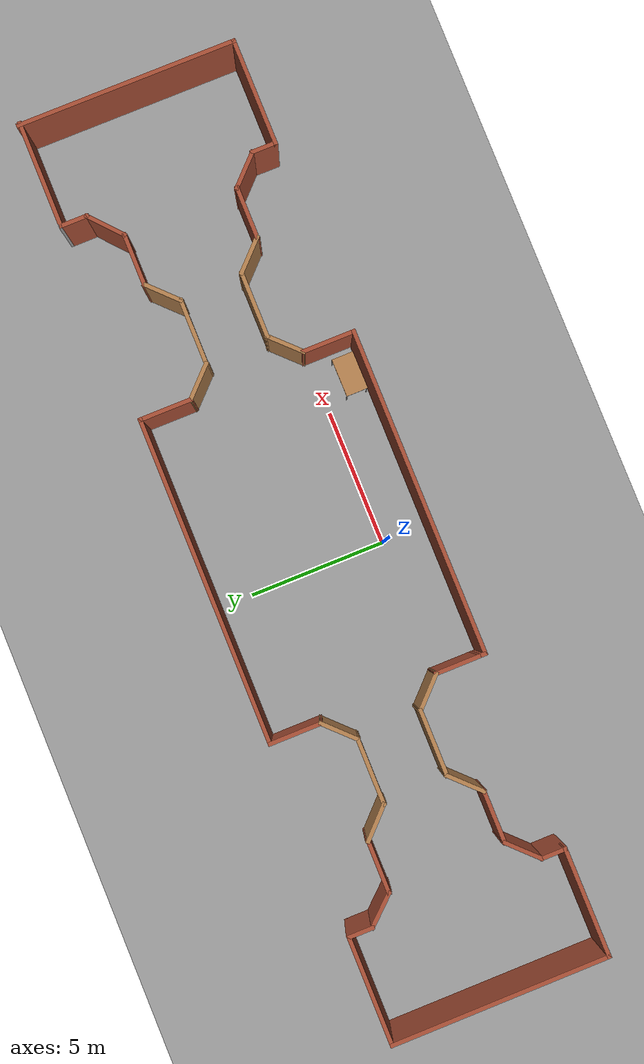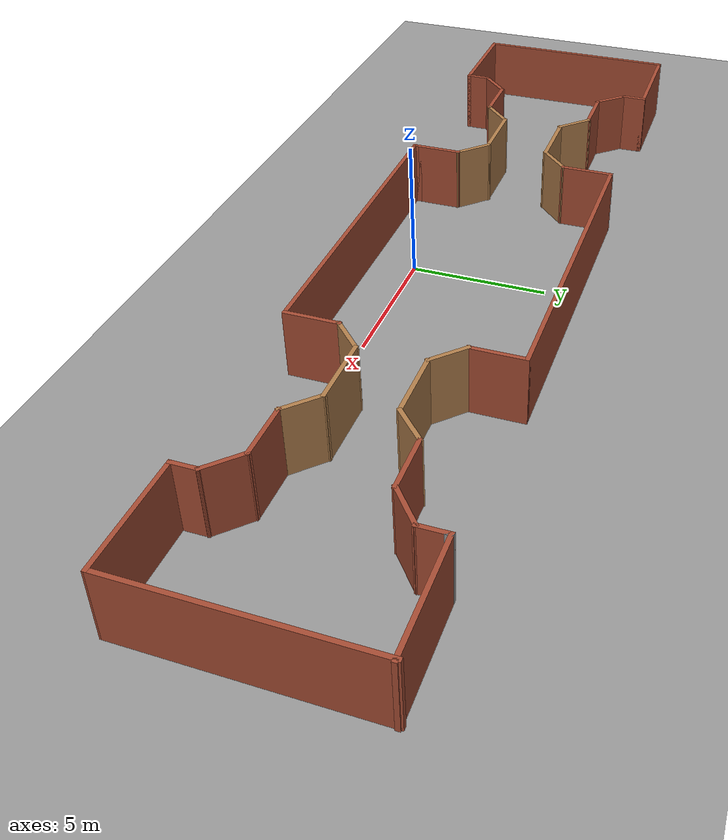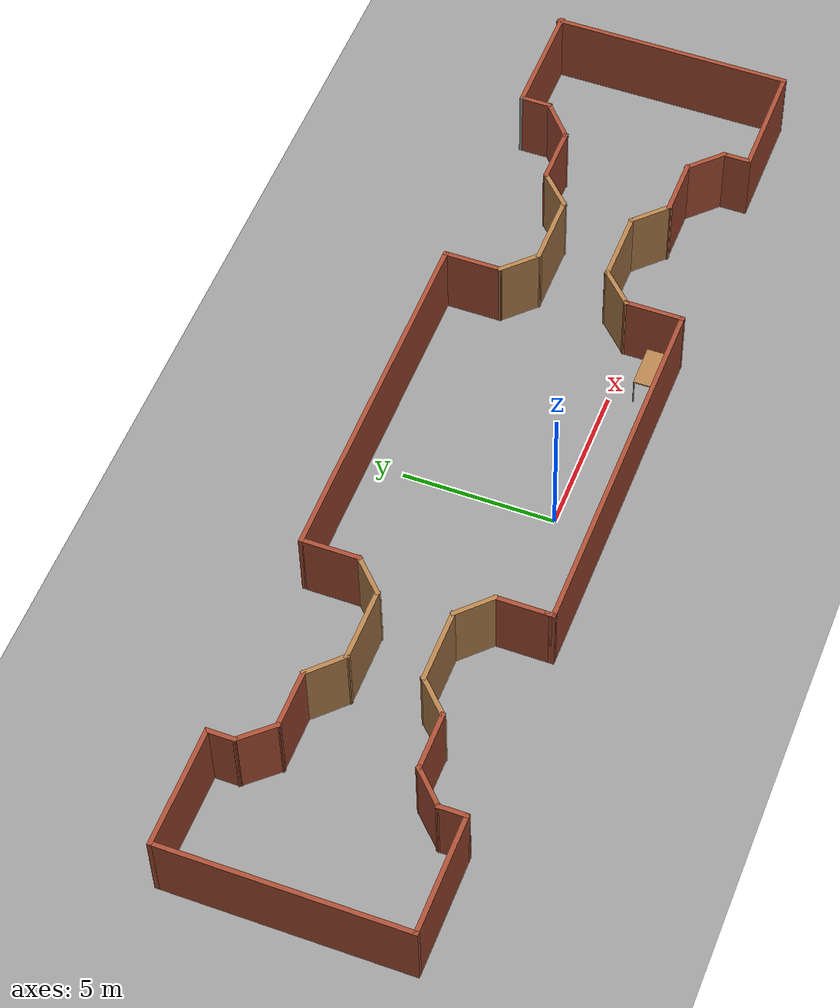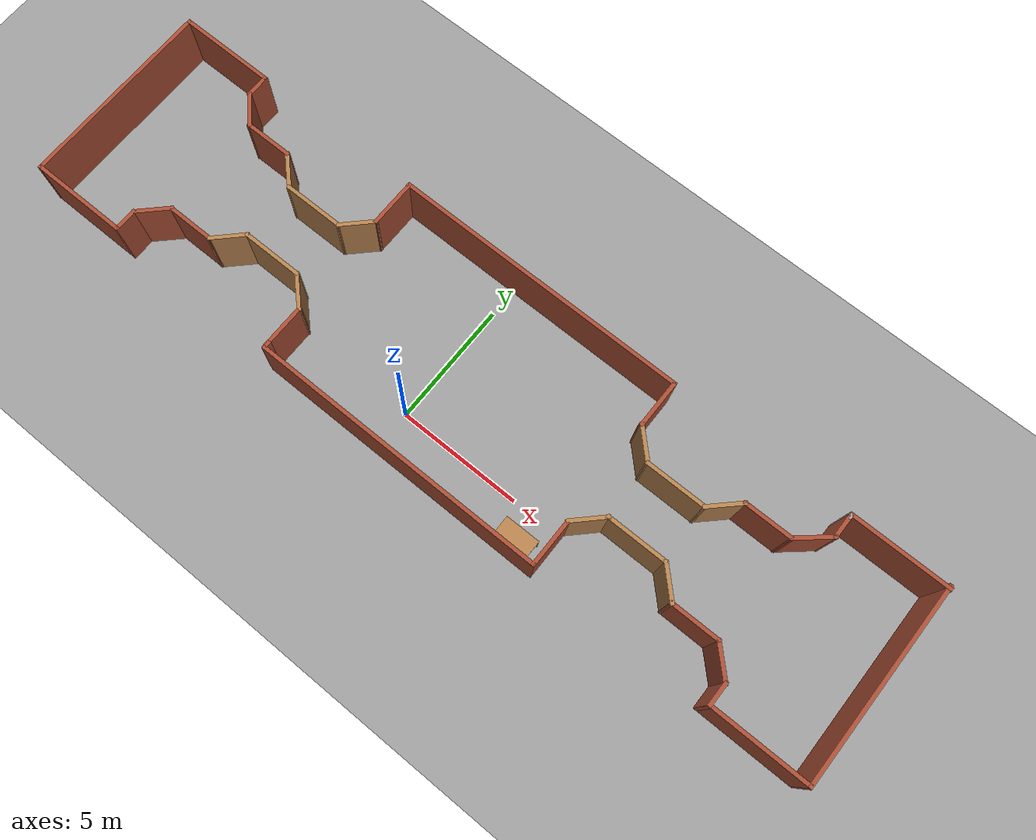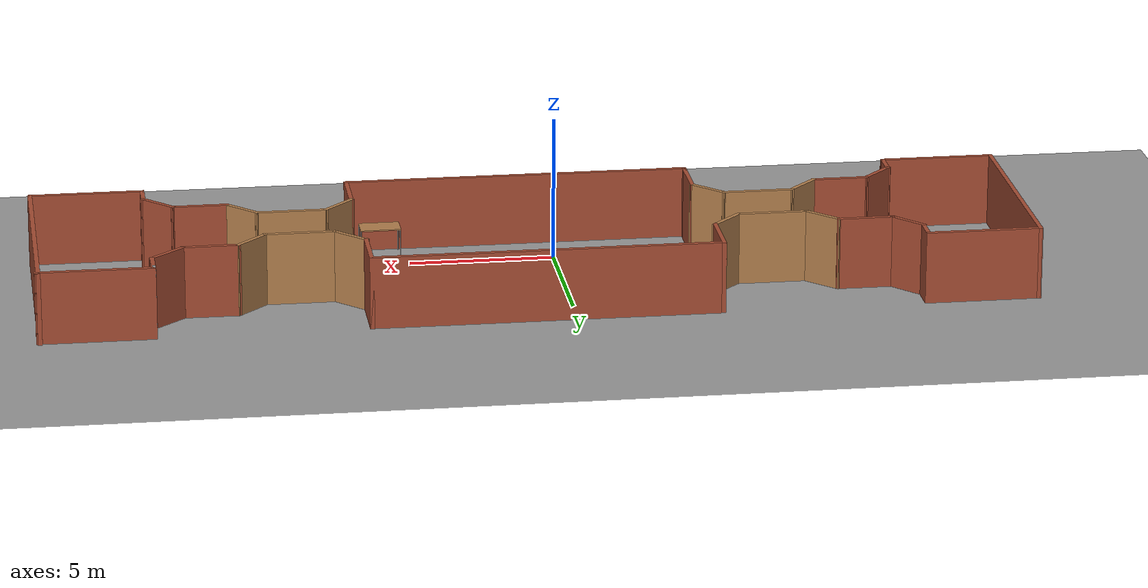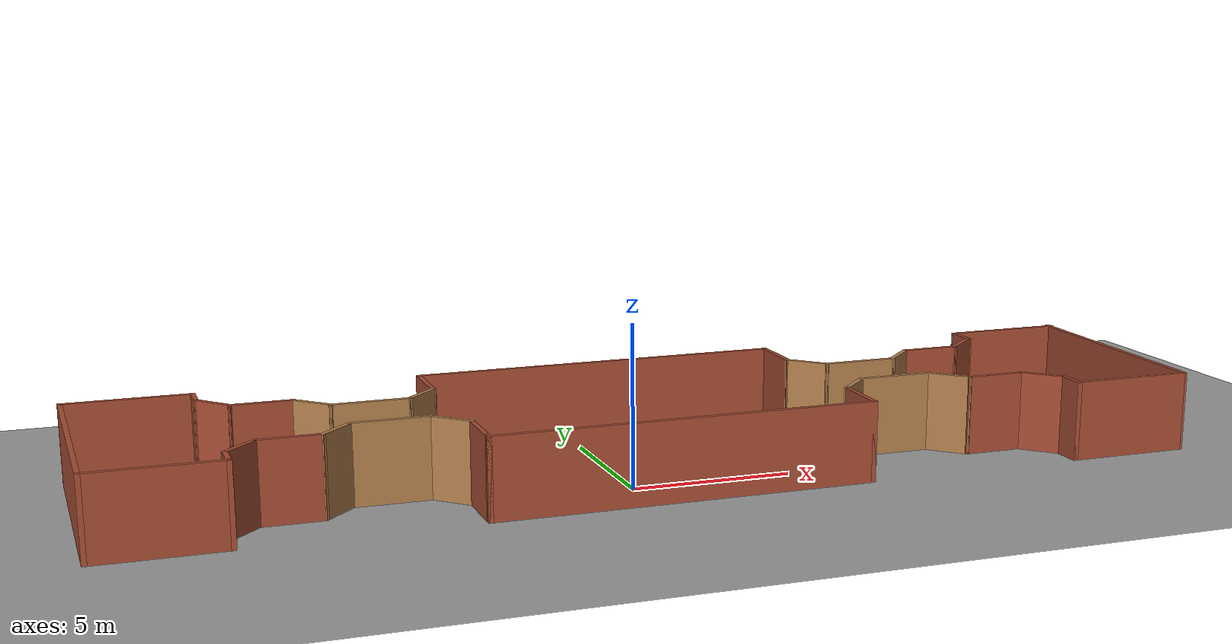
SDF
<sdf version="1.6">
 <world name="default">
  <light name="sun" type="directional">
   <pose>0 0 10 0 -0 0</pose>
   <diffuse>0.8 0.8 0.8 1</diffuse>
   <specular>0.1 0.1 0.1 1</specular>
   <attenuation>
    <range>1000</range>
    <constant>0.9</constant>
    <linear>0.01</linear>
    <quadratic>0.001</quadratic>
   </attenuation>
   <direction>-0.5 0.5 -1</direction>
  </light>
  <gravity>0 0 -9.8</gravity>
  <magnetic_field>6e-06 2.3e-05 -4.2e-05</magnetic_field>
  <atmosphere type="adiabatic"/>
  <physics name="default_physics" default="0" type="ode">
   <max_step_size>0.001</max_step_size>
   <real_time_factor>1</real_time_factor>
   <real_time_update_rate>1000</real_time_update_rate>
  </physics>
  <scene><ambient>0.4 0.4 0.4 1</ambient><background>0.7 0.7 0.7 1</background><shadows>1</shadows></scene>
  <spherical_coordinates>
   <surface_model>EARTH_WGS84</surface_model>
   <latitude_deg>0</latitude_deg>
   <longitude_deg>0</longitude_deg>
   <elevation>0</elevation>
   <heading_deg>0</heading_deg>
  </spherical_coordinates>
  <model name="table">
   <static>0</static>
   <link name="link">
    <collision name="surface">
     <pose>0 0 1 0 -0 0</pose>
     <geometry><box><size>1.5 0.8 0.03</size></box></geometry>
     <surface><friction><ode><mu>0.6</mu><mu2>0.6</mu2></ode></friction></surface>
    </collision>
    <visual name="visual1">
     <pose>0 0 1 0 -0 0</pose>
     <geometry><box><size>1.4 0.8 0.04</size></box></geometry>
     <material>
      <script><uri>file://media/materials/scripts/gazebo.material</uri><name>Gazebo/Wood</name></script>
     </material>
    </visual>
    <collision name="front_left_leg">
     <pose>0.68 0.38 0.5 0 -0 0</pose>
     <geometry><cylinder><radius>0.02</radius><length>1</length></cylinder></geometry>
    </collision>
    <visual name="front_left_leg">
     <pose>0.68 0.38 0.5 0 -0 0</pose>
     <geometry><cylinder><radius>0.02</radius><length>1</length></cylinder></geometry>
     <material>
      <script><uri>file://media/materials/scripts/gazebo.material</uri><name>Gazebo/Grey</name></script>
     </material>
    </visual>
    <collision name="front_right_leg">
     <pose>0.68 -0.38 0.5 0 -0 0</pose>
     <geometry><cylinder><radius>0.02</radius><length>1</length></cylinder></geometry>
    </collision>
    <visual name="front_right_leg">
     <pose>0.68 -0.38 0.5 0 -0 0</pose>
     <geometry><cylinder><radius>0.02</radius><length>1</length></cylinder></geometry>
     <material>
      <script><uri>file://media/materials/scripts/gazebo.material</uri><name>Gazebo/Grey</name></script>
     </material>
    </visual>
    <collision name="back_right_leg">
     <pose>-0.68 -0.38 0.5 0 -0 0</pose>
     <geometry><cylinder><radius>0.02</radius><length>1</length></cylinder></geometry>
    </collision>
    <visual name="back_right_leg">
     <pose>-0.68 -0.38 0.5 0 -0 0</pose>
     <geometry><cylinder><radius>0.02</radius><length>1</length></cylinder></geometry>
     <material>
      <script><uri>file://media/materials/scripts/gazebo.material</uri><name>Gazebo/Grey</name></script>
     </material>
    </visual>
    <collision name="back_left_leg">
     <pose>-0.68 0.38 0.5 0 -0 0</pose>
     <geometry><cylinder><radius>0.02</radius><length>1</length></cylinder></geometry>
    </collision>
    <visual name="back_left_leg">
     <pose>-0.68 0.38 0.5 0 -0 0</pose>
     <geometry><cylinder><radius>0.02</radius><length>1</length></cylinder></geometry>
     <material>
      <script><uri>file://media/materials/scripts/gazebo.material</uri><name>Gazebo/Grey</name></script>
     </material>
    </visual>
    <inertial>
     <inertia><ixx>1</ixx><ixy>0</ixy><ixz>0</ixz><iyy>1</iyy><iyz>0</iyz><izz>1</izz></inertia>
     <mass>1</mass>
    </inertial>
   </link>
   <pose>5.92545 -1.12492 -7e-06 -0 4e-06 0.006025</pose>
  </model>
  <model name="ground_plane_0">
   <static>1</static>
   <link name="link">
    <collision name="collision">
     <geometry><plane><normal>0 0 1</normal><size>100 100</size></plane></geometry>
     <surface><friction><ode><mu>100</mu><mu2>50</mu2></ode></friction></surface>
    </collision>
    <visual name="visual">
     <cast_shadows>0</cast_shadows>
     <geometry><plane><normal>0 0 1</normal><size>100 100</size></plane></geometry>
     <material>
      <script><uri>file://media/materials/scripts/gazebo.material</uri><name>Gazebo/Grey</name></script>
     </material>
    </visual>
   </link>
   <pose>-18.1806 -4.02372 0 0 -0 0</pose>
  </model>
  <model name="NewEnv1_0">
   <link name="Wall_12">
    <pose>-16.8734 -0.082813 0 0 0 -1.5708</pose>
    <visual name="Wall_12_Visual">
     <pose>0 0 1.25 0 -0 0</pose>
     <geometry><box><size>8 0.15 2.5</size></box></geometry>
     <material>
      <script><uri>file://media/materials/scripts/gazebo.material</uri><name>Gazebo/Bricks</name></script>
      <ambient>1 1 1 1</ambient>
      <diffuse>1 1 1 1</diffuse>
      <specular>0.2 0.2 0.2 1</specular>
      <emissive>0 0 0 1</emissive>
     </material>
    </visual>
    <collision name="Wall_12_Collision">
     <pose>0 0 1.25 0 -0 0</pose>
     <geometry><box><size>8 0.15 2.5</size></box></geometry>
     <surface>
      <friction>
       <ode><mu>1</mu><mu2>1</mu2><fdir1>0 0 0</fdir1><slip1>0</slip1><slip2>0</slip2></ode>
       <torsional>
        <coefficient>1</coefficient>
        <patch_radius>0</patch_radius>
        <surface_radius>0</surface_radius>
        <use_patch_radius>1</use_patch_radius>
        <ode><slip>0</slip></ode>
       </torsional>
      </friction>
      <bounce><restitution_coefficient>0</restitution_coefficient><threshold>1e+06</threshold></bounce>
      <contact>
       <collide_without_contact>0</collide_without_contact>
       <collide_without_contact_bitmask>1</collide_without_contact_bitmask>
       <collide_bitmask>1</collide_bitmask>
       <ode>
        <soft_cfm>0</soft_cfm>
        <soft_erp>0.2</soft_erp>
        <kp>1e+13</kp>
        <kd>1</kd>
        <max_vel>0.01</max_vel>
        <min_depth>0</min_depth>
       </ode>
       <bullet>
        <split_impulse>1</split_impulse>
        <split_impulse_penetration_threshold>-0.01</split_impulse_penetration_threshold>
        <soft_cfm>0</soft_cfm>
        <soft_erp>0.2</soft_erp>
        <kp>1e+13</kp>
        <kd>1</kd>
       </bullet>
      </contact>
     </surface>
    </collision>
   </link>
   <link name="Wall_13">
    <pose>-14.9484 -4.00781 0 0 -0 0</pose>
    <visual name="Wall_13_Visual">
     <pose>0 0 1.25 0 -0 0</pose>
     <geometry><box><size>4 0.15 2.5</size></box></geometry>
     <material>
      <script><uri>file://media/materials/scripts/gazebo.material</uri><name>Gazebo/Bricks</name></script>
      <ambient>1 1 1 1</ambient>
      <diffuse>1 1 1 1</diffuse>
      <specular>0.2 0.2 0.2 1</specular>
      <emissive>0 0 0 1</emissive>
     </material>
    </visual>
    <collision name="Wall_13_Collision">
     <pose>0 0 1.25 0 -0 0</pose>
     <geometry><box><size>4 0.15 2.5</size></box></geometry>
     <surface>
      <friction>
       <ode><mu>1</mu><mu2>1</mu2><fdir1>0 0 0</fdir1><slip1>0</slip1><slip2>0</slip2></ode>
       <torsional>
        <coefficient>1</coefficient>
        <patch_radius>0</patch_radius>
        <surface_radius>0</surface_radius>
        <use_patch_radius>1</use_patch_radius>
        <ode><slip>0</slip></ode>
       </torsional>
      </friction>
      <bounce><restitution_coefficient>0</restitution_coefficient><threshold>1e+06</threshold></bounce>
      <contact>
       <collide_without_contact>0</collide_without_contact>
       <collide_without_contact_bitmask>1</collide_without_contact_bitmask>
       <collide_bitmask>1</collide_bitmask>
       <ode>
        <soft_cfm>0</soft_cfm>
        <soft_erp>0.2</soft_erp>
        <kp>1e+13</kp>
        <kd>1</kd>
        <max_vel>0.01</max_vel>
        <min_depth>0</min_depth>
       </ode>
       <bullet>
        <split_impulse>1</split_impulse>
        <split_impulse_penetration_threshold>-0.01</split_impulse_penetration_threshold>
        <soft_cfm>0</soft_cfm>
        <soft_erp>0.2</soft_erp>
        <kp>1e+13</kp>
        <kd>1</kd>
       </bullet>
      </contact>
     </surface>
    </collision>
   </link>
   <link name="Wall_14">
    <pose>-13.0234 -3.58281 0 0 -0 1.5708</pose>
    <visual name="Wall_14_Visual">
     <pose>0 0 1.25 0 -0 0</pose>
     <geometry><box><size>1 0.15 2.5</size></box></geometry>
     <material>
      <script><uri>file://media/materials/scripts/gazebo.material</uri><name>Gazebo/Bricks</name></script>
      <ambient>1 1 1 1</ambient>
      <diffuse>1 1 1 1</diffuse>
      <specular>0.2 0.2 0.2 1</specular>
      <emissive>0 0 0 1</emissive>
     </material>
    </visual>
    <collision name="Wall_14_Collision">
     <pose>0 0 1.25 0 -0 0</pose>
     <geometry><box><size>1 0.15 2.5</size></box></geometry>
     <surface>
      <friction>
       <ode><mu>1</mu><mu2>1</mu2><fdir1>0 0 0</fdir1><slip1>0</slip1><slip2>0</slip2></ode>
       <torsional>
        <coefficient>1</coefficient>
        <patch_radius>0</patch_radius>
        <surface_radius>0</surface_radius>
        <use_patch_radius>1</use_patch_radius>
        <ode><slip>0</slip></ode>
       </torsional>
      </friction>
      <bounce><restitution_coefficient>0</restitution_coefficient><threshold>1e+06</threshold></bounce>
      <contact>
       <collide_without_contact>0</collide_without_contact>
       <collide_without_contact_bitmask>1</collide_without_contact_bitmask>
       <collide_bitmask>1</collide_bitmask>
       <ode>
        <soft_cfm>0</soft_cfm>
        <soft_erp>0.2</soft_erp>
        <kp>1e+13</kp>
        <kd>1</kd>
        <max_vel>0.01</max_vel>
        <min_depth>0</min_depth>
       </ode>
       <bullet>
        <split_impulse>1</split_impulse>
        <split_impulse_penetration_threshold>-0.01</split_impulse_penetration_threshold>
        <soft_cfm>0</soft_cfm>
        <soft_erp>0.2</soft_erp>
        <kp>1e+13</kp>
        <kd>1</kd>
       </bullet>
      </contact>
     </surface>
    </collision>
   </link>
   <link name="Wall_15">
    <pose>-12.5461 -2.68052 0 0 -0 0.785398</pose>
    <visual name="Wall_15_Visual">
     <pose>0 0 1.25 0 -0 0</pose>
     <geometry><box><size>1.5 0.15 2.5</size></box></geometry>
     <material>
      <script><uri>file://media/materials/scripts/gazebo.material</uri><name>Gazebo/Bricks</name></script>
      <ambient>1 1 1 1</ambient>
      <diffuse>1 1 1 1</diffuse>
      <specular>0.2 0.2 0.2 1</specular>
      <emissive>0 0 0 1</emissive>
     </material>
    </visual>
    <collision name="Wall_15_Collision">
     <pose>0 0 1.25 0 -0 0</pose>
     <geometry><box><size>1.5 0.15 2.5</size></box></geometry>
     <surface>
      <friction>
       <ode><mu>1</mu><mu2>1</mu2><fdir1>0 0 0</fdir1><slip1>0</slip1><slip2>0</slip2></ode>
       <torsional>
        <coefficient>1</coefficient>
        <patch_radius>0</patch_radius>
        <surface_radius>0</surface_radius>
        <use_patch_radius>1</use_patch_radius>
        <ode><slip>0</slip></ode>
       </torsional>
      </friction>
      <bounce><restitution_coefficient>0</restitution_coefficient><threshold>1e+06</threshold></bounce>
      <contact>
       <collide_without_contact>0</collide_without_contact>
       <collide_without_contact_bitmask>1</collide_without_contact_bitmask>
       <collide_bitmask>1</collide_bitmask>
       <ode>
        <soft_cfm>0</soft_cfm>
        <soft_erp>0.2</soft_erp>
        <kp>1e+13</kp>
        <kd>1</kd>
        <max_vel>0.01</max_vel>
        <min_depth>0</min_depth>
       </ode>
       <bullet>
        <split_impulse>1</split_impulse>
        <split_impulse_penetration_threshold>-0.01</split_impulse_penetration_threshold>
        <soft_cfm>0</soft_cfm>
        <soft_erp>0.2</soft_erp>
        <kp>1e+13</kp>
        <kd>1</kd>
       </bullet>
      </contact>
     </surface>
    </collision>
   </link>
   <link name="Wall_16">
    <pose>-11.1438 -2.20322 0 0 -0 0</pose>
    <visual name="Wall_16_Visual">
     <pose>0 0 1.25 0 -0 0</pose>
     <geometry><box><size>2 0.15 2.5</size></box></geometry>
     <material>
      <script><uri>file://media/materials/scripts/gazebo.material</uri><name>Gazebo/Bricks</name></script>
      <ambient>1 1 1 1</ambient>
      <diffuse>1 1 1 1</diffuse>
      <specular>0.2 0.2 0.2 1</specular>
      <emissive>0 0 0 1</emissive>
     </material>
    </visual>
    <collision name="Wall_16_Collision">
     <pose>0 0 1.25 0 -0 0</pose>
     <geometry><box><size>2 0.15 2.5</size></box></geometry>
     <surface>
      <friction>
       <ode><mu>1</mu><mu2>1</mu2><fdir1>0 0 0</fdir1><slip1>0</slip1><slip2>0</slip2></ode>
       <torsional>
        <coefficient>1</coefficient>
        <patch_radius>0</patch_radius>
        <surface_radius>0</surface_radius>
        <use_patch_radius>1</use_patch_radius>
        <ode><slip>0</slip></ode>
       </torsional>
      </friction>
      <bounce><restitution_coefficient>0</restitution_coefficient><threshold>1e+06</threshold></bounce>
      <contact>
       <collide_without_contact>0</collide_without_contact>
       <collide_without_contact_bitmask>1</collide_without_contact_bitmask>
       <collide_bitmask>1</collide_bitmask>
       <ode>
        <soft_cfm>0</soft_cfm>
        <soft_erp>0.2</soft_erp>
        <kp>1e+13</kp>
        <kd>1</kd>
        <max_vel>0.01</max_vel>
        <min_depth>0</min_depth>
       </ode>
       <bullet>
        <split_impulse>1</split_impulse>
        <split_impulse_penetration_threshold>-0.01</split_impulse_penetration_threshold>
        <soft_cfm>0</soft_cfm>
        <soft_erp>0.2</soft_erp>
        <kp>1e+13</kp>
        <kd>1</kd>
       </bullet>
      </contact>
     </surface>
    </collision>
   </link>
   <link name="Wall_17">
    <pose>-9.74146 -1.72592 0 0 -0 0.785398</pose>
    <visual name="Wall_17_Visual">
     <pose>0 0 1.25 0 -0 0</pose>
     <geometry><box><size>1.5 0.15 2.5</size></box></geometry>
     <material>
      <script><uri>file://media/materials/scripts/gazebo.material</uri><name>Gazebo/Wood</name></script>
      <ambient>1 1 1 1</ambient>
      <diffuse>1 1 1 1</diffuse>
      <specular>0.2 0.2 0.2 1</specular>
      <emissive>0 0 0 1</emissive>
     </material>
    </visual>
    <collision name="Wall_17_Collision">
     <pose>0 0 1.25 0 -0 0</pose>
     <geometry><box><size>1.5 0.15 2.5</size></box></geometry>
     <surface>
      <friction>
       <ode><mu>1</mu><mu2>1</mu2><fdir1>0 0 0</fdir1><slip1>0</slip1><slip2>0</slip2></ode>
       <torsional>
        <coefficient>1</coefficient>
        <patch_radius>0</patch_radius>
        <surface_radius>0</surface_radius>
        <use_patch_radius>1</use_patch_radius>
        <ode><slip>0</slip></ode>
       </torsional>
      </friction>
      <bounce><restitution_coefficient>0</restitution_coefficient><threshold>1e+06</threshold></bounce>
      <contact>
       <collide_without_contact>0</collide_without_contact>
       <collide_without_contact_bitmask>1</collide_without_contact_bitmask>
       <collide_bitmask>1</collide_bitmask>
       <ode>
        <soft_cfm>0</soft_cfm>
        <soft_erp>0.2</soft_erp>
        <kp>1e+13</kp>
        <kd>1</kd>
        <max_vel>0.01</max_vel>
        <min_depth>0</min_depth>
       </ode>
       <bullet>
        <split_impulse>1</split_impulse>
        <split_impulse_penetration_threshold>-0.01</split_impulse_penetration_threshold>
        <soft_cfm>0</soft_cfm>
        <soft_erp>0.2</soft_erp>
        <kp>1e+13</kp>
        <kd>1</kd>
       </bullet>
      </contact>
     </surface>
    </collision>
   </link>
   <link name="Wall_19">
    <pose>-8.08916 -1.24863 0 0 -0 0</pose>
    <visual name="Wall_19_Visual">
     <pose>0 0 1.25 0 -0 0</pose>
     <geometry><box><size>2.5 0.15 2.5</size></box></geometry>
     <material>
      <script><uri>file://media/materials/scripts/gazebo.material</uri><name>Gazebo/Wood</name></script>
      <ambient>1 1 1 1</ambient>
      <diffuse>1 1 1 1</diffuse>
      <specular>0.2 0.2 0.2 1</specular>
      <emissive>0 0 0 1</emissive>
     </material>
    </visual>
    <collision name="Wall_19_Collision">
     <pose>0 0 1.25 0 -0 0</pose>
     <geometry><box><size>2.5 0.15 2.5</size></box></geometry>
     <surface>
      <friction>
       <ode><mu>1</mu><mu2>1</mu2><fdir1>0 0 0</fdir1><slip1>0</slip1><slip2>0</slip2></ode>
       <torsional>
        <coefficient>1</coefficient>
        <patch_radius>0</patch_radius>
        <surface_radius>0</surface_radius>
        <use_patch_radius>1</use_patch_radius>
        <ode><slip>0</slip></ode>
       </torsional>
      </friction>
      <bounce><restitution_coefficient>0</restitution_coefficient><threshold>1e+06</threshold></bounce>
      <contact>
       <collide_without_contact>0</collide_without_contact>
       <collide_without_contact_bitmask>1</collide_without_contact_bitmask>
       <collide_bitmask>1</collide_bitmask>
       <ode>
        <soft_cfm>0</soft_cfm>
        <soft_erp>0.2</soft_erp>
        <kp>1e+13</kp>
        <kd>1</kd>
        <max_vel>0.01</max_vel>
        <min_depth>0</min_depth>
       </ode>
       <bullet>
        <split_impulse>1</split_impulse>
        <split_impulse_penetration_threshold>-0.01</split_impulse_penetration_threshold>
        <soft_cfm>0</soft_cfm>
        <soft_erp>0.2</soft_erp>
        <kp>1e+13</kp>
        <kd>1</kd>
       </bullet>
      </contact>
     </surface>
    </collision>
   </link>
   <link name="Wall_20">
    <pose>-6.43687 -1.72592 0 0 0 -0.785398</pose>
    <visual name="Wall_20_Visual">
     <pose>0 0 1.25 0 -0 0</pose>
     <geometry><box><size>1.5 0.15 2.5</size></box></geometry>
     <material>
      <script><uri>file://media/materials/scripts/gazebo.material</uri><name>Gazebo/Wood</name></script>
      <ambient>1 1 1 1</ambient>
      <diffuse>1 1 1 1</diffuse>
      <specular>0.2 0.2 0.2 1</specular>
      <emissive>0 0 0 1</emissive>
     </material>
    </visual>
    <collision name="Wall_20_Collision">
     <pose>0 0 1.25 0 -0 0</pose>
     <geometry><box><size>1.5 0.15 2.5</size></box></geometry>
     <surface>
      <friction>
       <ode><mu>1</mu><mu2>1</mu2><fdir1>0 0 0</fdir1><slip1>0</slip1><slip2>0</slip2></ode>
       <torsional>
        <coefficient>1</coefficient>
        <patch_radius>0</patch_radius>
        <surface_radius>0</surface_radius>
        <use_patch_radius>1</use_patch_radius>
        <ode><slip>0</slip></ode>
       </torsional>
      </friction>
      <bounce><restitution_coefficient>0</restitution_coefficient><threshold>1e+06</threshold></bounce>
      <contact>
       <collide_without_contact>0</collide_without_contact>
       <collide_without_contact_bitmask>1</collide_without_contact_bitmask>
       <collide_bitmask>1</collide_bitmask>
       <ode>
        <soft_cfm>0</soft_cfm>
        <soft_erp>0.2</soft_erp>
        <kp>1e+13</kp>
        <kd>1</kd>
        <max_vel>0.01</max_vel>
        <min_depth>0</min_depth>
       </ode>
       <bullet>
        <split_impulse>1</split_impulse>
        <split_impulse_penetration_threshold>-0.01</split_impulse_penetration_threshold>
        <soft_cfm>0</soft_cfm>
        <soft_erp>0.2</soft_erp>
        <kp>1e+13</kp>
        <kd>1</kd>
       </bullet>
      </contact>
     </surface>
    </collision>
   </link>
   <link name="Wall_21">
    <pose>-5.95957 -3.00322 0 0 0 -1.5708</pose>
    <visual name="Wall_21_Visual">
     <pose>0 0 1.25 0 -0 0</pose>
     <geometry><box><size>1.75 0.15 2.5</size></box></geometry>
     <material>
      <script><uri>file://media/materials/scripts/gazebo.material</uri><name>Gazebo/Bricks</name></script>
      <ambient>1 1 1 1</ambient>
      <diffuse>1 1 1 1</diffuse>
      <specular>0.2 0.2 0.2 1</specular>
      <emissive>0 0 0 1</emissive>
     </material>
    </visual>
    <collision name="Wall_21_Collision">
     <pose>0 0 1.25 0 -0 0</pose>
     <geometry><box><size>1.75 0.15 2.5</size></box></geometry>
     <surface>
      <friction>
       <ode><mu>1</mu><mu2>1</mu2><fdir1>0 0 0</fdir1><slip1>0</slip1><slip2>0</slip2></ode>
       <torsional>
        <coefficient>1</coefficient>
        <patch_radius>0</patch_radius>
        <surface_radius>0</surface_radius>
        <use_patch_radius>1</use_patch_radius>
        <ode><slip>0</slip></ode>
       </torsional>
      </friction>
      <bounce><restitution_coefficient>0</restitution_coefficient><threshold>1e+06</threshold></bounce>
      <contact>
       <collide_without_contact>0</collide_without_contact>
       <collide_without_contact_bitmask>1</collide_without_contact_bitmask>
       <collide_bitmask>1</collide_bitmask>
       <ode>
        <soft_cfm>0</soft_cfm>
        <soft_erp>0.2</soft_erp>
        <kp>1e+13</kp>
        <kd>1</kd>
        <max_vel>0.01</max_vel>
        <min_depth>0</min_depth>
       </ode>
       <bullet>
        <split_impulse>1</split_impulse>
        <split_impulse_penetration_threshold>-0.01</split_impulse_penetration_threshold>
        <soft_cfm>0</soft_cfm>
        <soft_erp>0.2</soft_erp>
        <kp>1e+13</kp>
        <kd>1</kd>
       </bullet>
      </contact>
     </surface>
    </collision>
   </link>
   <link name="Wall_22">
    <pose>-5.95957 -3.85322 0 0 0 -1.5708</pose>
    <visual name="Wall_22_Visual">
     <pose>0 0 1.25 0 -0 0</pose>
     <geometry><box><size>0.25 0.15 2.5</size></box></geometry>
     <material>
      <script><uri>file://media/materials/scripts/gazebo.material</uri><name>Gazebo/Bricks</name></script>
      <ambient>1 1 1 1</ambient>
      <diffuse>1 1 1 1</diffuse>
      <specular>0.2 0.2 0.2 1</specular>
      <emissive>0 0 0 1</emissive>
     </material>
    </visual>
    <collision name="Wall_22_Collision">
     <pose>0 0 1.25 0 -0 0</pose>
     <geometry><box><size>0.25 0.15 2.5</size></box></geometry>
     <surface>
      <friction>
       <ode><mu>1</mu><mu2>1</mu2><fdir1>0 0 0</fdir1><slip1>0</slip1><slip2>0</slip2></ode>
       <torsional>
        <coefficient>1</coefficient>
        <patch_radius>0</patch_radius>
        <surface_radius>0</surface_radius>
        <use_patch_radius>1</use_patch_radius>
        <ode><slip>0</slip></ode>
       </torsional>
      </friction>
      <bounce><restitution_coefficient>0</restitution_coefficient><threshold>1e+06</threshold></bounce>
      <contact>
       <collide_without_contact>0</collide_without_contact>
       <collide_without_contact_bitmask>1</collide_without_contact_bitmask>
       <collide_bitmask>1</collide_bitmask>
       <ode>
        <soft_cfm>0</soft_cfm>
        <soft_erp>0.2</soft_erp>
        <kp>1e+13</kp>
        <kd>1</kd>
        <max_vel>0.01</max_vel>
        <min_depth>0</min_depth>
       </ode>
       <bullet>
        <split_impulse>1</split_impulse>
        <split_impulse_penetration_threshold>-0.01</split_impulse_penetration_threshold>
        <soft_cfm>0</soft_cfm>
        <soft_erp>0.2</soft_erp>
        <kp>1e+13</kp>
        <kd>1</kd>
       </bullet>
      </contact>
     </surface>
    </collision>
   </link>
   <link name="Wall_23">
    <pose>-5.95957 -3.95322 0 0 0 -1.5708</pose>
    <visual name="Wall_23_Visual">
     <pose>0 0 1.25 0 -0 0</pose>
     <geometry><box><size>0.25 0.15 2.5</size></box></geometry>
     <material>
      <script><uri>file://media/materials/scripts/gazebo.material</uri><name>Gazebo/Bricks</name></script>
      <ambient>1 1 1 1</ambient>
      <diffuse>1 1 1 1</diffuse>
      <specular>0.2 0.2 0.2 1</specular>
      <emissive>0 0 0 1</emissive>
     </material>
    </visual>
    <collision name="Wall_23_Collision">
     <pose>0 0 1.25 0 -0 0</pose>
     <geometry><box><size>0.25 0.15 2.5</size></box></geometry>
     <surface>
      <friction>
       <ode><mu>1</mu><mu2>1</mu2><fdir1>0 0 0</fdir1><slip1>0</slip1><slip2>0</slip2></ode>
       <torsional>
        <coefficient>1</coefficient>
        <patch_radius>0</patch_radius>
        <surface_radius>0</surface_radius>
        <use_patch_radius>1</use_patch_radius>
        <ode><slip>0</slip></ode>
       </torsional>
      </friction>
      <bounce><restitution_coefficient>0</restitution_coefficient><threshold>1e+06</threshold></bounce>
      <contact>
       <collide_without_contact>0</collide_without_contact>
       <collide_without_contact_bitmask>1</collide_without_contact_bitmask>
       <collide_bitmask>1</collide_bitmask>
       <ode>
        <soft_cfm>0</soft_cfm>
        <soft_erp>0.2</soft_erp>
        <kp>1e+13</kp>
        <kd>1</kd>
        <max_vel>0.01</max_vel>
        <min_depth>0</min_depth>
       </ode>
       <bullet>
        <split_impulse>1</split_impulse>
        <split_impulse_penetration_threshold>-0.01</split_impulse_penetration_threshold>
        <soft_cfm>0</soft_cfm>
        <soft_erp>0.2</soft_erp>
        <kp>1e+13</kp>
        <kd>1</kd>
       </bullet>
      </contact>
     </surface>
    </collision>
   </link>
   <link name="Wall_24">
    <pose>-0.034569 -4.00322 0 0 -0 0</pose>
    <visual name="Wall_24_Visual">
     <pose>0 0 1.25 0 -0 0</pose>
     <geometry><box><size>12 0.15 2.5</size></box></geometry>
     <material>
      <script><uri>file://media/materials/scripts/gazebo.material</uri><name>Gazebo/Bricks</name></script>
      <ambient>1 1 1 1</ambient>
      <diffuse>1 1 1 1</diffuse>
      <specular>0.2 0.2 0.2 1</specular>
      <emissive>0 0 0 1</emissive>
     </material>
    </visual>
    <collision name="Wall_24_Collision">
     <pose>0 0 1.25 0 -0 0</pose>
     <geometry><box><size>12 0.15 2.5</size></box></geometry>
     <surface>
      <friction>
       <ode><mu>1</mu><mu2>1</mu2><fdir1>0 0 0</fdir1><slip1>0</slip1><slip2>0</slip2></ode>
       <torsional>
        <coefficient>1</coefficient>
        <patch_radius>0</patch_radius>
        <surface_radius>0</surface_radius>
        <use_patch_radius>1</use_patch_radius>
        <ode><slip>0</slip></ode>
       </torsional>
      </friction>
      <bounce><restitution_coefficient>0</restitution_coefficient><threshold>1e+06</threshold></bounce>
      <contact>
       <collide_without_contact>0</collide_without_contact>
       <collide_without_contact_bitmask>1</collide_without_contact_bitmask>
       <collide_bitmask>1</collide_bitmask>
       <ode>
        <soft_cfm>0</soft_cfm>
        <soft_erp>0.2</soft_erp>
        <kp>1e+13</kp>
        <kd>1</kd>
        <max_vel>0.01</max_vel>
        <min_depth>0</min_depth>
       </ode>
       <bullet>
        <split_impulse>1</split_impulse>
        <split_impulse_penetration_threshold>-0.01</split_impulse_penetration_threshold>
        <soft_cfm>0</soft_cfm>
        <soft_erp>0.2</soft_erp>
        <kp>1e+13</kp>
        <kd>1</kd>
       </bullet>
      </contact>
     </surface>
    </collision>
   </link>
   <link name="Wall_25">
    <pose>5.89043 -3.07822 0 0 -0 1.5708</pose>
    <visual name="Wall_25_Visual">
     <pose>0 0 1.25 0 -0 0</pose>
     <geometry><box><size>2 0.15 2.5</size></box></geometry>
     <material>
      <script><uri>file://media/materials/scripts/gazebo.material</uri><name>Gazebo/Bricks</name></script>
      <ambient>1 1 1 1</ambient>
      <diffuse>1 1 1 1</diffuse>
      <specular>0.2 0.2 0.2 1</specular>
      <emissive>0 0 0 1</emissive>
     </material>
    </visual>
    <collision name="Wall_25_Collision">
     <pose>0 0 1.25 0 -0 0</pose>
     <geometry><box><size>2 0.15 2.5</size></box></geometry>
     <surface>
      <friction>
       <ode><mu>1</mu><mu2>1</mu2><fdir1>0 0 0</fdir1><slip1>0</slip1><slip2>0</slip2></ode>
       <torsional>
        <coefficient>1</coefficient>
        <patch_radius>0</patch_radius>
        <surface_radius>0</surface_radius>
        <use_patch_radius>1</use_patch_radius>
        <ode><slip>0</slip></ode>
       </torsional>
      </friction>
      <bounce><restitution_coefficient>0</restitution_coefficient><threshold>1e+06</threshold></bounce>
      <contact>
       <collide_without_contact>0</collide_without_contact>
       <collide_without_contact_bitmask>1</collide_without_contact_bitmask>
       <collide_bitmask>1</collide_bitmask>
       <ode>
        <soft_cfm>0</soft_cfm>
        <soft_erp>0.2</soft_erp>
        <kp>1e+13</kp>
        <kd>1</kd>
        <max_vel>0.01</max_vel>
        <min_depth>0</min_depth>
       </ode>
       <bullet>
        <split_impulse>1</split_impulse>
        <split_impulse_penetration_threshold>-0.01</split_impulse_penetration_threshold>
        <soft_cfm>0</soft_cfm>
        <soft_erp>0.2</soft_erp>
        <kp>1e+13</kp>
        <kd>1</kd>
       </bullet>
      </contact>
     </surface>
    </collision>
   </link>
   <link name="Wall_26">
    <pose>6.36773 -1.67592 0 0 -0 0.785398</pose>
    <visual name="Wall_26_Visual">
     <pose>0 0 1.25 0 -0 0</pose>
     <geometry><box><size>1.5 0.15 2.5</size></box></geometry>
     <material>
      <script><uri>file://media/materials/scripts/gazebo.material</uri><name>Gazebo/Wood</name></script>
      <ambient>1 1 1 1</ambient>
      <diffuse>1 1 1 1</diffuse>
      <specular>0.2 0.2 0.2 1</specular>
      <emissive>0 0 0 1</emissive>
     </material>
    </visual>
    <collision name="Wall_26_Collision">
     <pose>0 0 1.25 0 -0 0</pose>
     <geometry><box><size>1.5 0.15 2.5</size></box></geometry>
     <surface>
      <friction>
       <ode><mu>1</mu><mu2>1</mu2><fdir1>0 0 0</fdir1><slip1>0</slip1><slip2>0</slip2></ode>
       <torsional>
        <coefficient>1</coefficient>
        <patch_radius>0</patch_radius>
        <surface_radius>0</surface_radius>
        <use_patch_radius>1</use_patch_radius>
        <ode><slip>0</slip></ode>
       </torsional>
      </friction>
      <bounce><restitution_coefficient>0</restitution_coefficient><threshold>1e+06</threshold></bounce>
      <contact>
       <collide_without_contact>0</collide_without_contact>
       <collide_without_contact_bitmask>1</collide_without_contact_bitmask>
       <collide_bitmask>1</collide_bitmask>
       <ode>
        <soft_cfm>0</soft_cfm>
        <soft_erp>0.2</soft_erp>
        <kp>1e+13</kp>
        <kd>1</kd>
        <max_vel>0.01</max_vel>
        <min_depth>0</min_depth>
       </ode>
       <bullet>
        <split_impulse>1</split_impulse>
        <split_impulse_penetration_threshold>-0.01</split_impulse_penetration_threshold>
        <soft_cfm>0</soft_cfm>
        <soft_erp>0.2</soft_erp>
        <kp>1e+13</kp>
        <kd>1</kd>
       </bullet>
      </contact>
     </surface>
    </collision>
   </link>
   <link name="Wall_27">
    <pose>8.02003 -1.19863 0 0 -0 0</pose>
    <visual name="Wall_27_Visual">
     <pose>0 0 1.25 0 -0 0</pose>
     <geometry><box><size>2.5 0.15 2.5</size></box></geometry>
     <material>
      <script><uri>file://media/materials/scripts/gazebo.material</uri><name>Gazebo/Wood</name></script>
      <ambient>1 1 1 1</ambient>
      <diffuse>1 1 1 1</diffuse>
      <specular>0.2 0.2 0.2 1</specular>
      <emissive>0 0 0 1</emissive>
     </material>
    </visual>
    <collision name="Wall_27_Collision">
     <pose>0 0 1.25 0 -0 0</pose>
     <geometry><box><size>2.5 0.15 2.5</size></box></geometry>
     <surface>
      <friction>
       <ode><mu>1</mu><mu2>1</mu2><fdir1>0 0 0</fdir1><slip1>0</slip1><slip2>0</slip2></ode>
       <torsional>
        <coefficient>1</coefficient>
        <patch_radius>0</patch_radius>
        <surface_radius>0</surface_radius>
        <use_patch_radius>1</use_patch_radius>
        <ode><slip>0</slip></ode>
       </torsional>
      </friction>
      <bounce><restitution_coefficient>0</restitution_coefficient><threshold>1e+06</threshold></bounce>
      <contact>
       <collide_without_contact>0</collide_without_contact>
       <collide_without_contact_bitmask>1</collide_without_contact_bitmask>
       <collide_bitmask>1</collide_bitmask>
       <ode>
        <soft_cfm>0</soft_cfm>
        <soft_erp>0.2</soft_erp>
        <kp>1e+13</kp>
        <kd>1</kd>
        <max_vel>0.01</max_vel>
        <min_depth>0</min_depth>
       </ode>
       <bullet>
        <split_impulse>1</split_impulse>
        <split_impulse_penetration_threshold>-0.01</split_impulse_penetration_threshold>
        <soft_cfm>0</soft_cfm>
        <soft_erp>0.2</soft_erp>
        <kp>1e+13</kp>
        <kd>1</kd>
       </bullet>
      </contact>
     </surface>
    </collision>
   </link>
   <link name="Wall_28">
    <pose>9.67232 -1.67592 0 0 0 -0.785398</pose>
    <visual name="Wall_28_Visual">
     <pose>0 0 1.25 0 -0 0</pose>
     <geometry><box><size>1.5 0.15 2.5</size></box></geometry>
     <material>
      <script><uri>file://media/materials/scripts/gazebo.material</uri><name>Gazebo/Wood</name></script>
      <ambient>1 1 1 1</ambient>
      <diffuse>1 1 1 1</diffuse>
      <specular>0.2 0.2 0.2 1</specular>
      <emissive>0 0 0 1</emissive>
     </material>
    </visual>
    <collision name="Wall_28_Collision">
     <pose>0 0 1.25 0 -0 0</pose>
     <geometry><box><size>1.5 0.15 2.5</size></box></geometry>
     <surface>
      <friction>
       <ode><mu>1</mu><mu2>1</mu2><fdir1>0 0 0</fdir1><slip1>0</slip1><slip2>0</slip2></ode>
       <torsional>
        <coefficient>1</coefficient>
        <patch_radius>0</patch_radius>
        <surface_radius>0</surface_radius>
        <use_patch_radius>1</use_patch_radius>
        <ode><slip>0</slip></ode>
       </torsional>
      </friction>
      <bounce><restitution_coefficient>0</restitution_coefficient><threshold>1e+06</threshold></bounce>
      <contact>
       <collide_without_contact>0</collide_without_contact>
       <collide_without_contact_bitmask>1</collide_without_contact_bitmask>
       <collide_bitmask>1</collide_bitmask>
       <ode>
        <soft_cfm>0</soft_cfm>
        <soft_erp>0.2</soft_erp>
        <kp>1e+13</kp>
        <kd>1</kd>
        <max_vel>0.01</max_vel>
        <min_depth>0</min_depth>
       </ode>
       <bullet>
        <split_impulse>1</split_impulse>
        <split_impulse_penetration_threshold>-0.01</split_impulse_penetration_threshold>
        <soft_cfm>0</soft_cfm>
        <soft_erp>0.2</soft_erp>
        <kp>1e+13</kp>
        <kd>1</kd>
       </bullet>
      </contact>
     </surface>
    </collision>
   </link>
   <link name="Wall_29">
    <pose>11.0746 -2.15322 0 0 -0 0</pose>
    <visual name="Wall_29_Visual">
     <pose>0 0 1.25 0 -0 0</pose>
     <geometry><box><size>2 0.15 2.5</size></box></geometry>
     <material>
      <script><uri>file://media/materials/scripts/gazebo.material</uri><name>Gazebo/Bricks</name></script>
      <ambient>1 1 1 1</ambient>
      <diffuse>1 1 1 1</diffuse>
      <specular>0.2 0.2 0.2 1</specular>
      <emissive>0 0 0 1</emissive>
     </material>
    </visual>
    <collision name="Wall_29_Collision">
     <pose>0 0 1.25 0 -0 0</pose>
     <geometry><box><size>2 0.15 2.5</size></box></geometry>
     <surface>
      <friction>
       <ode><mu>1</mu><mu2>1</mu2><fdir1>0 0 0</fdir1><slip1>0</slip1><slip2>0</slip2></ode>
       <torsional>
        <coefficient>1</coefficient>
        <patch_radius>0</patch_radius>
        <surface_radius>0</surface_radius>
        <use_patch_radius>1</use_patch_radius>
        <ode><slip>0</slip></ode>
       </torsional>
      </friction>
      <bounce><restitution_coefficient>0</restitution_coefficient><threshold>1e+06</threshold></bounce>
      <contact>
       <collide_without_contact>0</collide_without_contact>
       <collide_without_contact_bitmask>1</collide_without_contact_bitmask>
       <collide_bitmask>1</collide_bitmask>
       <ode>
        <soft_cfm>0</soft_cfm>
        <soft_erp>0.2</soft_erp>
        <kp>1e+13</kp>
        <kd>1</kd>
        <max_vel>0.01</max_vel>
        <min_depth>0</min_depth>
       </ode>
       <bullet>
        <split_impulse>1</split_impulse>
        <split_impulse_penetration_threshold>-0.01</split_impulse_penetration_threshold>
        <soft_cfm>0</soft_cfm>
        <soft_erp>0.2</soft_erp>
        <kp>1e+13</kp>
        <kd>1</kd>
       </bullet>
      </contact>
     </surface>
    </collision>
   </link>
   <link name="Wall_30">
    <pose>12.4769 -2.63052 0 0 0 -0.785398</pose>
    <visual name="Wall_30_Visual">
     <pose>0 0 1.25 0 -0 0</pose>
     <geometry><box><size>1.5 0.15 2.5</size></box></geometry>
     <material>
      <script><uri>file://media/materials/scripts/gazebo.material</uri><name>Gazebo/Bricks</name></script>
      <ambient>1 1 1 1</ambient>
      <diffuse>1 1 1 1</diffuse>
      <specular>0.2 0.2 0.2 1</specular>
      <emissive>0 0 0 1</emissive>
     </material>
    </visual>
    <collision name="Wall_30_Collision">
     <pose>0 0 1.25 0 -0 0</pose>
     <geometry><box><size>1.5 0.15 2.5</size></box></geometry>
     <surface>
      <friction>
       <ode><mu>1</mu><mu2>1</mu2><fdir1>0 0 0</fdir1><slip1>0</slip1><slip2>0</slip2></ode>
       <torsional>
        <coefficient>1</coefficient>
        <patch_radius>0</patch_radius>
        <surface_radius>0</surface_radius>
        <use_patch_radius>1</use_patch_radius>
        <ode><slip>0</slip></ode>
       </torsional>
      </friction>
      <bounce><restitution_coefficient>0</restitution_coefficient><threshold>1e+06</threshold></bounce>
      <contact>
       <collide_without_contact>0</collide_without_contact>
       <collide_without_contact_bitmask>1</collide_without_contact_bitmask>
       <collide_bitmask>1</collide_bitmask>
       <ode>
        <soft_cfm>0</soft_cfm>
        <soft_erp>0.2</soft_erp>
        <kp>1e+13</kp>
        <kd>1</kd>
        <max_vel>0.01</max_vel>
        <min_depth>0</min_depth>
       </ode>
       <bullet>
        <split_impulse>1</split_impulse>
        <split_impulse_penetration_threshold>-0.01</split_impulse_penetration_threshold>
        <soft_cfm>0</soft_cfm>
        <soft_erp>0.2</soft_erp>
        <kp>1e+13</kp>
        <kd>1</kd>
       </bullet>
      </contact>
     </surface>
    </collision>
   </link>
   <link name="Wall_31">
    <pose>12.9542 -3.53281 0 0 0 -1.5708</pose>
    <visual name="Wall_31_Visual">
     <pose>0 0 1.25 0 -0 0</pose>
     <geometry><box><size>1 0.15 2.5</size></box></geometry>
     <material>
      <script><uri>file://media/materials/scripts/gazebo.material</uri><name>Gazebo/Bricks</name></script>
      <ambient>1 1 1 1</ambient>
      <diffuse>1 1 1 1</diffuse>
      <specular>0.2 0.2 0.2 1</specular>
      <emissive>0 0 0 1</emissive>
     </material>
    </visual>
    <collision name="Wall_31_Collision">
     <pose>0 0 1.25 0 -0 0</pose>
     <geometry><box><size>1 0.15 2.5</size></box></geometry>
     <surface>
      <friction>
       <ode><mu>1</mu><mu2>1</mu2><fdir1>0 0 0</fdir1><slip1>0</slip1><slip2>0</slip2></ode>
       <torsional>
        <coefficient>1</coefficient>
        <patch_radius>0</patch_radius>
        <surface_radius>0</surface_radius>
        <use_patch_radius>1</use_patch_radius>
        <ode><slip>0</slip></ode>
       </torsional>
      </friction>
      <bounce><restitution_coefficient>0</restitution_coefficient><threshold>1e+06</threshold></bounce>
      <contact>
       <collide_without_contact>0</collide_without_contact>
       <collide_without_contact_bitmask>1</collide_without_contact_bitmask>
       <collide_bitmask>1</collide_bitmask>
       <ode>
        <soft_cfm>0</soft_cfm>
        <soft_erp>0.2</soft_erp>
        <kp>1e+13</kp>
        <kd>1</kd>
        <max_vel>0.01</max_vel>
        <min_depth>0</min_depth>
       </ode>
       <bullet>
        <split_impulse>1</split_impulse>
        <split_impulse_penetration_threshold>-0.01</split_impulse_penetration_threshold>
        <soft_cfm>0</soft_cfm>
        <soft_erp>0.2</soft_erp>
        <kp>1e+13</kp>
        <kd>1</kd>
       </bullet>
      </contact>
     </surface>
    </collision>
   </link>
   <link name="Wall_32">
    <pose>14.8792 -3.95781 0 0 -0 0</pose>
    <visual name="Wall_32_Visual">
     <pose>0 0 1.25 0 -0 0</pose>
     <geometry><box><size>4 0.15 2.5</size></box></geometry>
     <material>
      <script><uri>file://media/materials/scripts/gazebo.material</uri><name>Gazebo/Bricks</name></script>
      <ambient>1 1 1 1</ambient>
      <diffuse>1 1 1 1</diffuse>
      <specular>0.2 0.2 0.2 1</specular>
      <emissive>0 0 0 1</emissive>
     </material>
    </visual>
    <collision name="Wall_32_Collision">
     <pose>0 0 1.25 0 -0 0</pose>
     <geometry><box><size>4 0.15 2.5</size></box></geometry>
     <surface>
      <friction>
       <ode><mu>1</mu><mu2>1</mu2><fdir1>0 0 0</fdir1><slip1>0</slip1><slip2>0</slip2></ode>
       <torsional>
        <coefficient>1</coefficient>
        <patch_radius>0</patch_radius>
        <surface_radius>0</surface_radius>
        <use_patch_radius>1</use_patch_radius>
        <ode><slip>0</slip></ode>
       </torsional>
      </friction>
      <bounce><restitution_coefficient>0</restitution_coefficient><threshold>1e+06</threshold></bounce>
      <contact>
       <collide_without_contact>0</collide_without_contact>
       <collide_without_contact_bitmask>1</collide_without_contact_bitmask>
       <collide_bitmask>1</collide_bitmask>
       <ode>
        <soft_cfm>0</soft_cfm>
        <soft_erp>0.2</soft_erp>
        <kp>1e+13</kp>
        <kd>1</kd>
        <max_vel>0.01</max_vel>
        <min_depth>0</min_depth>
       </ode>
       <bullet>
        <split_impulse>1</split_impulse>
        <split_impulse_penetration_threshold>-0.01</split_impulse_penetration_threshold>
        <soft_cfm>0</soft_cfm>
        <soft_erp>0.2</soft_erp>
        <kp>1e+13</kp>
        <kd>1</kd>
       </bullet>
      </contact>
     </surface>
    </collision>
   </link>
   <link name="Wall_33">
    <pose>16.8172 0.024879 0 0 -0 1.56755</pose>
    <visual name="Wall_33_Visual">
     <pose>0 0 1.25 0 -0 0</pose>
     <geometry><box><size>8.11543 0.15 2.5</size></box></geometry>
     <material>
      <script><uri>file://media/materials/scripts/gazebo.material</uri><name>Gazebo/Bricks</name></script>
      <ambient>1 1 1 1</ambient>
      <diffuse>1 1 1 1</diffuse>
      <specular>0.2 0.2 0.2 1</specular>
      <emissive>0 0 0 1</emissive>
     </material>
    </visual>
    <collision name="Wall_33_Collision">
     <pose>0 0 1.25 0 -0 0</pose>
     <geometry><box><size>8.11543 0.15 2.5</size></box></geometry>
     <surface>
      <friction>
       <ode><mu>1</mu><mu2>1</mu2><fdir1>0 0 0</fdir1><slip1>0</slip1><slip2>0</slip2></ode>
       <torsional>
        <coefficient>1</coefficient>
        <patch_radius>0</patch_radius>
        <surface_radius>0</surface_radius>
        <use_patch_radius>1</use_patch_radius>
        <ode><slip>0</slip></ode>
       </torsional>
      </friction>
      <bounce><restitution_coefficient>0</restitution_coefficient><threshold>1e+06</threshold></bounce>
      <contact>
       <collide_without_contact>0</collide_without_contact>
       <collide_without_contact_bitmask>1</collide_without_contact_bitmask>
       <collide_bitmask>1</collide_bitmask>
       <ode>
        <soft_cfm>0</soft_cfm>
        <soft_erp>0.2</soft_erp>
        <kp>1e+13</kp>
        <kd>1</kd>
        <max_vel>0.01</max_vel>
        <min_depth>0</min_depth>
       </ode>
       <bullet>
        <split_impulse>1</split_impulse>
        <split_impulse_penetration_threshold>-0.01</split_impulse_penetration_threshold>
        <soft_cfm>0</soft_cfm>
        <soft_erp>0.2</soft_erp>
        <kp>1e+13</kp>
        <kd>1</kd>
       </bullet>
      </contact>
     </surface>
    </collision>
   </link>
   <link name="Wall_47">
    <pose>-14.9484 3.84219 0 0 -0 0</pose>
    <visual name="Wall_47_Visual">
     <pose>0 0 1.25 0 -0 0</pose>
     <geometry><box><size>4 0.15 2.5</size></box></geometry>
     <material>
      <script><uri>file://media/materials/scripts/gazebo.material</uri><name>Gazebo/Bricks</name></script>
      <ambient>1 1 1 1</ambient>
      <diffuse>1 1 1 1</diffuse>
      <specular>0.2 0.2 0.2 1</specular>
      <emissive>0 0 0 1</emissive>
     </material>
    </visual>
    <collision name="Wall_47_Collision">
     <pose>0 0 1.25 0 -0 0</pose>
     <geometry><box><size>4 0.15 2.5</size></box></geometry>
     <surface>
      <friction>
       <ode><mu>1</mu><mu2>1</mu2><fdir1>0 0 0</fdir1><slip1>0</slip1><slip2>0</slip2></ode>
       <torsional>
        <coefficient>1</coefficient>
        <patch_radius>0</patch_radius>
        <surface_radius>0</surface_radius>
        <use_patch_radius>1</use_patch_radius>
        <ode><slip>0</slip></ode>
       </torsional>
      </friction>
      <bounce><restitution_coefficient>0</restitution_coefficient><threshold>1e+06</threshold></bounce>
      <contact>
       <collide_without_contact>0</collide_without_contact>
       <collide_without_contact_bitmask>1</collide_without_contact_bitmask>
       <collide_bitmask>1</collide_bitmask>
       <ode>
        <soft_cfm>0</soft_cfm>
        <soft_erp>0.2</soft_erp>
        <kp>1e+13</kp>
        <kd>1</kd>
        <max_vel>0.01</max_vel>
        <min_depth>0</min_depth>
       </ode>
       <bullet>
        <split_impulse>1</split_impulse>
        <split_impulse_penetration_threshold>-0.01</split_impulse_penetration_threshold>
        <soft_cfm>0</soft_cfm>
        <soft_erp>0.2</soft_erp>
        <kp>1e+13</kp>
        <kd>1</kd>
       </bullet>
      </contact>
     </surface>
    </collision>
   </link>
   <link name="Wall_48">
    <pose>-13.0234 3.41719 0 0 0 -1.5708</pose>
    <visual name="Wall_48_Visual">
     <pose>0 0 1.25 0 -0 0</pose>
     <geometry><box><size>1 0.15 2.5</size></box></geometry>
     <material>
      <script><uri>file://media/materials/scripts/gazebo.material</uri><name>Gazebo/Bricks</name></script>
      <ambient>1 1 1 1</ambient>
      <diffuse>1 1 1 1</diffuse>
      <specular>0.2 0.2 0.2 1</specular>
      <emissive>0 0 0 1</emissive>
     </material>
    </visual>
    <collision name="Wall_48_Collision">
     <pose>0 0 1.25 0 -0 0</pose>
     <geometry><box><size>1 0.15 2.5</size></box></geometry>
     <surface>
      <friction>
       <ode><mu>1</mu><mu2>1</mu2><fdir1>0 0 0</fdir1><slip1>0</slip1><slip2>0</slip2></ode>
       <torsional>
        <coefficient>1</coefficient>
        <patch_radius>0</patch_radius>
        <surface_radius>0</surface_radius>
        <use_patch_radius>1</use_patch_radius>
        <ode><slip>0</slip></ode>
       </torsional>
      </friction>
      <bounce><restitution_coefficient>0</restitution_coefficient><threshold>1e+06</threshold></bounce>
      <contact>
       <collide_without_contact>0</collide_without_contact>
       <collide_without_contact_bitmask>1</collide_without_contact_bitmask>
       <collide_bitmask>1</collide_bitmask>
       <ode>
        <soft_cfm>0</soft_cfm>
        <soft_erp>0.2</soft_erp>
        <kp>1e+13</kp>
        <kd>1</kd>
        <max_vel>0.01</max_vel>
        <min_depth>0</min_depth>
       </ode>
       <bullet>
        <split_impulse>1</split_impulse>
        <split_impulse_penetration_threshold>-0.01</split_impulse_penetration_threshold>
        <soft_cfm>0</soft_cfm>
        <soft_erp>0.2</soft_erp>
        <kp>1e+13</kp>
        <kd>1</kd>
       </bullet>
      </contact>
     </surface>
    </collision>
   </link>
   <link name="Wall_49">
    <pose>-12.5919 2.51489 0 0 0 -0.83585</pose>
    <visual name="Wall_49_Visual">
     <pose>0 0 1.25 0 -0 0</pose>
     <geometry><box><size>1.43675 0.15 2.5</size></box></geometry>
     <material>
      <script><uri>file://media/materials/scripts/gazebo.material</uri><name>Gazebo/Bricks</name></script>
      <ambient>1 1 1 1</ambient>
      <diffuse>1 1 1 1</diffuse>
      <specular>0.2 0.2 0.2 1</specular>
      <emissive>0 0 0 1</emissive>
     </material>
    </visual>
    <collision name="Wall_49_Collision">
     <pose>0 0 1.25 0 -0 0</pose>
     <geometry><box><size>1.43675 0.15 2.5</size></box></geometry>
     <surface>
      <friction>
       <ode><mu>1</mu><mu2>1</mu2><fdir1>0 0 0</fdir1><slip1>0</slip1><slip2>0</slip2></ode>
       <torsional>
        <coefficient>1</coefficient>
        <patch_radius>0</patch_radius>
        <surface_radius>0</surface_radius>
        <use_patch_radius>1</use_patch_radius>
        <ode><slip>0</slip></ode>
       </torsional>
      </friction>
      <bounce><restitution_coefficient>0</restitution_coefficient><threshold>1e+06</threshold></bounce>
      <contact>
       <collide_without_contact>0</collide_without_contact>
       <collide_without_contact_bitmask>1</collide_without_contact_bitmask>
       <collide_bitmask>1</collide_bitmask>
       <ode>
        <soft_cfm>0</soft_cfm>
        <soft_erp>0.2</soft_erp>
        <kp>1e+13</kp>
        <kd>1</kd>
        <max_vel>0.01</max_vel>
        <min_depth>0</min_depth>
       </ode>
       <bullet>
        <split_impulse>1</split_impulse>
        <split_impulse_penetration_threshold>-0.01</split_impulse_penetration_threshold>
        <soft_cfm>0</soft_cfm>
        <soft_erp>0.2</soft_erp>
        <kp>1e+13</kp>
        <kd>1</kd>
       </bullet>
      </contact>
     </surface>
    </collision>
   </link>
   <link name="Wall_52">
    <pose>-11.2355 2.03759 0 0 -0 0</pose>
    <visual name="Wall_52_Visual">
     <pose>0 0 1.25 0 -0 0</pose>
     <geometry><box><size>2 0.15 2.5</size></box></geometry>
     <material>
      <script><uri>file://media/materials/scripts/gazebo.material</uri><name>Gazebo/Bricks</name></script>
      <ambient>1 1 1 1</ambient>
      <diffuse>1 1 1 1</diffuse>
      <specular>0.2 0.2 0.2 1</specular>
      <emissive>0 0 0 1</emissive>
     </material>
    </visual>
    <collision name="Wall_52_Collision">
     <pose>0 0 1.25 0 -0 0</pose>
     <geometry><box><size>2 0.15 2.5</size></box></geometry>
     <surface>
      <friction>
       <ode><mu>1</mu><mu2>1</mu2><fdir1>0 0 0</fdir1><slip1>0</slip1><slip2>0</slip2></ode>
       <torsional>
        <coefficient>1</coefficient>
        <patch_radius>0</patch_radius>
        <surface_radius>0</surface_radius>
        <use_patch_radius>1</use_patch_radius>
        <ode><slip>0</slip></ode>
       </torsional>
      </friction>
      <bounce><restitution_coefficient>0</restitution_coefficient><threshold>1e+06</threshold></bounce>
      <contact>
       <collide_without_contact>0</collide_without_contact>
       <collide_without_contact_bitmask>1</collide_without_contact_bitmask>
       <collide_bitmask>1</collide_bitmask>
       <ode>
        <soft_cfm>0</soft_cfm>
        <soft_erp>0.2</soft_erp>
        <kp>1e+13</kp>
        <kd>1</kd>
        <max_vel>0.01</max_vel>
        <min_depth>0</min_depth>
       </ode>
       <bullet>
        <split_impulse>1</split_impulse>
        <split_impulse_penetration_threshold>-0.01</split_impulse_penetration_threshold>
        <soft_cfm>0</soft_cfm>
        <soft_erp>0.2</soft_erp>
        <kp>1e+13</kp>
        <kd>1</kd>
       </bullet>
      </contact>
     </surface>
    </collision>
   </link>
   <link name="Wall_53">
    <pose>-9.83323 1.5603 0 0 0 -0.785398</pose>
    <visual name="Wall_53_Visual">
     <pose>0 0 1.25 0 -0 0</pose>
     <geometry><box><size>1.5 0.15 2.5</size></box></geometry>
     <material>
      <script><uri>file://media/materials/scripts/gazebo.material</uri><name>Gazebo/Wood</name></script>
      <ambient>1 1 1 1</ambient>
      <diffuse>1 1 1 1</diffuse>
      <specular>0.2 0.2 0.2 1</specular>
      <emissive>0 0 0 1</emissive>
     </material>
    </visual>
    <collision name="Wall_53_Collision">
     <pose>0 0 1.25 0 -0 0</pose>
     <geometry><box><size>1.5 0.15 2.5</size></box></geometry>
     <surface>
      <friction>
       <ode><mu>1</mu><mu2>1</mu2><fdir1>0 0 0</fdir1><slip1>0</slip1><slip2>0</slip2></ode>
       <torsional>
        <coefficient>1</coefficient>
        <patch_radius>0</patch_radius>
        <surface_radius>0</surface_radius>
        <use_patch_radius>1</use_patch_radius>
        <ode><slip>0</slip></ode>
       </torsional>
      </friction>
      <bounce><restitution_coefficient>0</restitution_coefficient><threshold>1e+06</threshold></bounce>
      <contact>
       <collide_without_contact>0</collide_without_contact>
       <collide_without_contact_bitmask>1</collide_without_contact_bitmask>
       <collide_bitmask>1</collide_bitmask>
       <ode>
        <soft_cfm>0</soft_cfm>
        <soft_erp>0.2</soft_erp>
        <kp>1e+13</kp>
        <kd>1</kd>
        <max_vel>0.01</max_vel>
        <min_depth>0</min_depth>
       </ode>
       <bullet>
        <split_impulse>1</split_impulse>
        <split_impulse_penetration_threshold>-0.01</split_impulse_penetration_threshold>
        <soft_cfm>0</soft_cfm>
        <soft_erp>0.2</soft_erp>
        <kp>1e+13</kp>
        <kd>1</kd>
       </bullet>
      </contact>
     </surface>
    </collision>
   </link>
   <link name="Wall_54">
    <pose>-8.18093 1.083 0 0 -0 0</pose>
    <visual name="Wall_54_Visual">
     <pose>0 0 1.25 0 -0 0</pose>
     <geometry><box><size>2.5 0.15 2.5</size></box></geometry>
     <material>
      <script><uri>file://media/materials/scripts/gazebo.material</uri><name>Gazebo/Wood</name></script>
      <ambient>1 1 1 1</ambient>
      <diffuse>1 1 1 1</diffuse>
      <specular>0.2 0.2 0.2 1</specular>
      <emissive>0 0 0 1</emissive>
     </material>
    </visual>
    <collision name="Wall_54_Collision">
     <pose>0 0 1.25 0 -0 0</pose>
     <geometry><box><size>2.5 0.15 2.5</size></box></geometry>
     <surface>
      <friction>
       <ode><mu>1</mu><mu2>1</mu2><fdir1>0 0 0</fdir1><slip1>0</slip1><slip2>0</slip2></ode>
       <torsional>
        <coefficient>1</coefficient>
        <patch_radius>0</patch_radius>
        <surface_radius>0</surface_radius>
        <use_patch_radius>1</use_patch_radius>
        <ode><slip>0</slip></ode>
       </torsional>
      </friction>
      <bounce><restitution_coefficient>0</restitution_coefficient><threshold>1e+06</threshold></bounce>
      <contact>
       <collide_without_contact>0</collide_without_contact>
       <collide_without_contact_bitmask>1</collide_without_contact_bitmask>
       <collide_bitmask>1</collide_bitmask>
       <ode>
        <soft_cfm>0</soft_cfm>
        <soft_erp>0.2</soft_erp>
        <kp>1e+13</kp>
        <kd>1</kd>
        <max_vel>0.01</max_vel>
        <min_depth>0</min_depth>
       </ode>
       <bullet>
        <split_impulse>1</split_impulse>
        <split_impulse_penetration_threshold>-0.01</split_impulse_penetration_threshold>
        <soft_cfm>0</soft_cfm>
        <soft_erp>0.2</soft_erp>
        <kp>1e+13</kp>
        <kd>1</kd>
       </bullet>
      </contact>
     </surface>
    </collision>
   </link>
   <link name="Wall_55">
    <pose>-6.52864 1.5603 0 0 -0 0.785398</pose>
    <visual name="Wall_55_Visual">
     <pose>0 0 1.25 0 -0 0</pose>
     <geometry><box><size>1.5 0.15 2.5</size></box></geometry>
     <material>
      <script><uri>file://media/materials/scripts/gazebo.material</uri><name>Gazebo/Wood</name></script>
      <ambient>1 1 1 1</ambient>
      <diffuse>1 1 1 1</diffuse>
      <specular>0.2 0.2 0.2 1</specular>
      <emissive>0 0 0 1</emissive>
     </material>
    </visual>
    <collision name="Wall_55_Collision">
     <pose>0 0 1.25 0 -0 0</pose>
     <geometry><box><size>1.5 0.15 2.5</size></box></geometry>
     <surface>
      <friction>
       <ode><mu>1</mu><mu2>1</mu2><fdir1>0 0 0</fdir1><slip1>0</slip1><slip2>0</slip2></ode>
       <torsional>
        <coefficient>1</coefficient>
        <patch_radius>0</patch_radius>
        <surface_radius>0</surface_radius>
        <use_patch_radius>1</use_patch_radius>
        <ode><slip>0</slip></ode>
       </torsional>
      </friction>
      <bounce><restitution_coefficient>0</restitution_coefficient><threshold>1e+06</threshold></bounce>
      <contact>
       <collide_without_contact>0</collide_without_contact>
       <collide_without_contact_bitmask>1</collide_without_contact_bitmask>
       <collide_bitmask>1</collide_bitmask>
       <ode>
        <soft_cfm>0</soft_cfm>
        <soft_erp>0.2</soft_erp>
        <kp>1e+13</kp>
        <kd>1</kd>
        <max_vel>0.01</max_vel>
        <min_depth>0</min_depth>
       </ode>
       <bullet>
        <split_impulse>1</split_impulse>
        <split_impulse_penetration_threshold>-0.01</split_impulse_penetration_threshold>
        <soft_cfm>0</soft_cfm>
        <soft_erp>0.2</soft_erp>
        <kp>1e+13</kp>
        <kd>1</kd>
       </bullet>
      </contact>
     </surface>
    </collision>
   </link>
   <link name="Wall_56">
    <pose>-6.05134 2.96259 0 0 -0 1.5708</pose>
    <visual name="Wall_56_Visual">
     <pose>0 0 1.25 0 -0 0</pose>
     <geometry><box><size>2 0.15 2.5</size></box></geometry>
     <material>
      <script><uri>file://media/materials/scripts/gazebo.material</uri><name>Gazebo/Bricks</name></script>
      <ambient>1 1 1 1</ambient>
      <diffuse>1 1 1 1</diffuse>
      <specular>0.2 0.2 0.2 1</specular>
      <emissive>0 0 0 1</emissive>
     </material>
    </visual>
    <collision name="Wall_56_Collision">
     <pose>0 0 1.25 0 -0 0</pose>
     <geometry><box><size>2 0.15 2.5</size></box></geometry>
     <surface>
      <friction>
       <ode><mu>1</mu><mu2>1</mu2><fdir1>0 0 0</fdir1><slip1>0</slip1><slip2>0</slip2></ode>
       <torsional>
        <coefficient>1</coefficient>
        <patch_radius>0</patch_radius>
        <surface_radius>0</surface_radius>
        <use_patch_radius>1</use_patch_radius>
        <ode><slip>0</slip></ode>
       </torsional>
      </friction>
      <bounce><restitution_coefficient>0</restitution_coefficient><threshold>1e+06</threshold></bounce>
      <contact>
       <collide_without_contact>0</collide_without_contact>
       <collide_without_contact_bitmask>1</collide_without_contact_bitmask>
       <collide_bitmask>1</collide_bitmask>
       <ode>
        <soft_cfm>0</soft_cfm>
        <soft_erp>0.2</soft_erp>
        <kp>1e+13</kp>
        <kd>1</kd>
        <max_vel>0.01</max_vel>
        <min_depth>0</min_depth>
       </ode>
       <bullet>
        <split_impulse>1</split_impulse>
        <split_impulse_penetration_threshold>-0.01</split_impulse_penetration_threshold>
        <soft_cfm>0</soft_cfm>
        <soft_erp>0.2</soft_erp>
        <kp>1e+13</kp>
        <kd>1</kd>
       </bullet>
      </contact>
     </surface>
    </collision>
   </link>
   <link name="Wall_57">
    <pose>-0.12634 3.88759 0 0 -0 0</pose>
    <visual name="Wall_57_Visual">
     <pose>0 0 1.25 0 -0 0</pose>
     <geometry><box><size>12 0.15 2.5</size></box></geometry>
     <material>
      <script><uri>file://media/materials/scripts/gazebo.material</uri><name>Gazebo/Bricks</name></script>
      <ambient>1 1 1 1</ambient>
      <diffuse>1 1 1 1</diffuse>
      <specular>0.2 0.2 0.2 1</specular>
      <emissive>0 0 0 1</emissive>
     </material>
    </visual>
    <collision name="Wall_57_Collision">
     <pose>0 0 1.25 0 -0 0</pose>
     <geometry><box><size>12 0.15 2.5</size></box></geometry>
     <surface>
      <friction>
       <ode><mu>1</mu><mu2>1</mu2><fdir1>0 0 0</fdir1><slip1>0</slip1><slip2>0</slip2></ode>
       <torsional>
        <coefficient>1</coefficient>
        <patch_radius>0</patch_radius>
        <surface_radius>0</surface_radius>
        <use_patch_radius>1</use_patch_radius>
        <ode><slip>0</slip></ode>
       </torsional>
      </friction>
      <bounce><restitution_coefficient>0</restitution_coefficient><threshold>1e+06</threshold></bounce>
      <contact>
       <collide_without_contact>0</collide_without_contact>
       <collide_without_contact_bitmask>1</collide_without_contact_bitmask>
       <collide_bitmask>1</collide_bitmask>
       <ode>
        <soft_cfm>0</soft_cfm>
        <soft_erp>0.2</soft_erp>
        <kp>1e+13</kp>
        <kd>1</kd>
        <max_vel>0.01</max_vel>
        <min_depth>0</min_depth>
       </ode>
       <bullet>
        <split_impulse>1</split_impulse>
        <split_impulse_penetration_threshold>-0.01</split_impulse_penetration_threshold>
        <soft_cfm>0</soft_cfm>
        <soft_erp>0.2</soft_erp>
        <kp>1e+13</kp>
        <kd>1</kd>
       </bullet>
      </contact>
     </surface>
    </collision>
   </link>
   <link name="Wall_58">
    <pose>5.79866 2.96259 0 0 0 -1.5708</pose>
    <visual name="Wall_58_Visual">
     <pose>0 0 1.25 0 -0 0</pose>
     <geometry><box><size>2 0.15 2.5</size></box></geometry>
     <material>
      <script><uri>file://media/materials/scripts/gazebo.material</uri><name>Gazebo/Bricks</name></script>
      <ambient>1 1 1 1</ambient>
      <diffuse>1 1 1 1</diffuse>
      <specular>0.2 0.2 0.2 1</specular>
      <emissive>0 0 0 1</emissive>
     </material>
    </visual>
    <collision name="Wall_58_Collision">
     <pose>0 0 1.25 0 -0 0</pose>
     <geometry><box><size>2 0.15 2.5</size></box></geometry>
     <surface>
      <friction>
       <ode><mu>1</mu><mu2>1</mu2><fdir1>0 0 0</fdir1><slip1>0</slip1><slip2>0</slip2></ode>
       <torsional>
        <coefficient>1</coefficient>
        <patch_radius>0</patch_radius>
        <surface_radius>0</surface_radius>
        <use_patch_radius>1</use_patch_radius>
        <ode><slip>0</slip></ode>
       </torsional>
      </friction>
      <bounce><restitution_coefficient>0</restitution_coefficient><threshold>1e+06</threshold></bounce>
      <contact>
       <collide_without_contact>0</collide_without_contact>
       <collide_without_contact_bitmask>1</collide_without_contact_bitmask>
       <collide_bitmask>1</collide_bitmask>
       <ode>
        <soft_cfm>0</soft_cfm>
        <soft_erp>0.2</soft_erp>
        <kp>1e+13</kp>
        <kd>1</kd>
        <max_vel>0.01</max_vel>
        <min_depth>0</min_depth>
       </ode>
       <bullet>
        <split_impulse>1</split_impulse>
        <split_impulse_penetration_threshold>-0.01</split_impulse_penetration_threshold>
        <soft_cfm>0</soft_cfm>
        <soft_erp>0.2</soft_erp>
        <kp>1e+13</kp>
        <kd>1</kd>
       </bullet>
      </contact>
     </surface>
    </collision>
   </link>
   <link name="Wall_59">
    <pose>6.27596 1.5603 0 0 0 -0.785398</pose>
    <visual name="Wall_59_Visual">
     <pose>0 0 1.25 0 -0 0</pose>
     <geometry><box><size>1.5 0.15 2.5</size></box></geometry>
     <material>
      <script><uri>file://media/materials/scripts/gazebo.material</uri><name>Gazebo/Wood</name></script>
      <ambient>1 1 1 1</ambient>
      <diffuse>1 1 1 1</diffuse>
      <specular>0.2 0.2 0.2 1</specular>
      <emissive>0 0 0 1</emissive>
     </material>
    </visual>
    <collision name="Wall_59_Collision">
     <pose>0 0 1.25 0 -0 0</pose>
     <geometry><box><size>1.5 0.15 2.5</size></box></geometry>
     <surface>
      <friction>
       <ode><mu>1</mu><mu2>1</mu2><fdir1>0 0 0</fdir1><slip1>0</slip1><slip2>0</slip2></ode>
       <torsional>
        <coefficient>1</coefficient>
        <patch_radius>0</patch_radius>
        <surface_radius>0</surface_radius>
        <use_patch_radius>1</use_patch_radius>
        <ode><slip>0</slip></ode>
       </torsional>
      </friction>
      <bounce><restitution_coefficient>0</restitution_coefficient><threshold>1e+06</threshold></bounce>
      <contact>
       <collide_without_contact>0</collide_without_contact>
       <collide_without_contact_bitmask>1</collide_without_contact_bitmask>
       <collide_bitmask>1</collide_bitmask>
       <ode>
        <soft_cfm>0</soft_cfm>
        <soft_erp>0.2</soft_erp>
        <kp>1e+13</kp>
        <kd>1</kd>
        <max_vel>0.01</max_vel>
        <min_depth>0</min_depth>
       </ode>
       <bullet>
        <split_impulse>1</split_impulse>
        <split_impulse_penetration_threshold>-0.01</split_impulse_penetration_threshold>
        <soft_cfm>0</soft_cfm>
        <soft_erp>0.2</soft_erp>
        <kp>1e+13</kp>
        <kd>1</kd>
       </bullet>
      </contact>
     </surface>
    </collision>
   </link>
   <link name="Wall_60">
    <pose>7.92826 1.083 0 0 -0 0</pose>
    <visual name="Wall_60_Visual">
     <pose>0 0 1.25 0 -0 0</pose>
     <geometry><box><size>2.5 0.15 2.5</size></box></geometry>
     <material>
      <script><uri>file://media/materials/scripts/gazebo.material</uri><name>Gazebo/Wood</name></script>
      <ambient>1 1 1 1</ambient>
      <diffuse>1 1 1 1</diffuse>
      <specular>0.2 0.2 0.2 1</specular>
      <emissive>0 0 0 1</emissive>
     </material>
    </visual>
    <collision name="Wall_60_Collision">
     <pose>0 0 1.25 0 -0 0</pose>
     <geometry><box><size>2.5 0.15 2.5</size></box></geometry>
     <surface>
      <friction>
       <ode><mu>1</mu><mu2>1</mu2><fdir1>0 0 0</fdir1><slip1>0</slip1><slip2>0</slip2></ode>
       <torsional>
        <coefficient>1</coefficient>
        <patch_radius>0</patch_radius>
        <surface_radius>0</surface_radius>
        <use_patch_radius>1</use_patch_radius>
        <ode><slip>0</slip></ode>
       </torsional>
      </friction>
      <bounce><restitution_coefficient>0</restitution_coefficient><threshold>1e+06</threshold></bounce>
      <contact>
       <collide_without_contact>0</collide_without_contact>
       <collide_without_contact_bitmask>1</collide_without_contact_bitmask>
       <collide_bitmask>1</collide_bitmask>
       <ode>
        <soft_cfm>0</soft_cfm>
        <soft_erp>0.2</soft_erp>
        <kp>1e+13</kp>
        <kd>1</kd>
        <max_vel>0.01</max_vel>
        <min_depth>0</min_depth>
       </ode>
       <bullet>
        <split_impulse>1</split_impulse>
        <split_impulse_penetration_threshold>-0.01</split_impulse_penetration_threshold>
        <soft_cfm>0</soft_cfm>
        <soft_erp>0.2</soft_erp>
        <kp>1e+13</kp>
        <kd>1</kd>
       </bullet>
      </contact>
     </surface>
    </collision>
   </link>
   <link name="Wall_61">
    <pose>9.59061 1.5603 0 0 -0 0.774973</pose>
    <visual name="Wall_61_Visual">
     <pose>0 0 1.25 0 -0 0</pose>
     <geometry><box><size>1.5143 0.15 2.5</size></box></geometry>
     <material>
      <script><uri>file://media/materials/scripts/gazebo.material</uri><name>Gazebo/Wood</name></script>
      <ambient>1 1 1 1</ambient>
      <diffuse>1 1 1 1</diffuse>
      <specular>0.2 0.2 0.2 1</specular>
      <emissive>0 0 0 1</emissive>
     </material>
    </visual>
    <collision name="Wall_61_Collision">
     <pose>0 0 1.25 0 -0 0</pose>
     <geometry><box><size>1.5143 0.15 2.5</size></box></geometry>
     <surface>
      <friction>
       <ode><mu>1</mu><mu2>1</mu2><fdir1>0 0 0</fdir1><slip1>0</slip1><slip2>0</slip2></ode>
       <torsional>
        <coefficient>1</coefficient>
        <patch_radius>0</patch_radius>
        <surface_radius>0</surface_radius>
        <use_patch_radius>1</use_patch_radius>
        <ode><slip>0</slip></ode>
       </torsional>
      </friction>
      <bounce><restitution_coefficient>0</restitution_coefficient><threshold>1e+06</threshold></bounce>
      <contact>
       <collide_without_contact>0</collide_without_contact>
       <collide_without_contact_bitmask>1</collide_without_contact_bitmask>
       <collide_bitmask>1</collide_bitmask>
       <ode>
        <soft_cfm>0</soft_cfm>
        <soft_erp>0.2</soft_erp>
        <kp>1e+13</kp>
        <kd>1</kd>
        <max_vel>0.01</max_vel>
        <min_depth>0</min_depth>
       </ode>
       <bullet>
        <split_impulse>1</split_impulse>
        <split_impulse_penetration_threshold>-0.01</split_impulse_penetration_threshold>
        <soft_cfm>0</soft_cfm>
        <soft_erp>0.2</soft_erp>
        <kp>1e+13</kp>
        <kd>1</kd>
       </bullet>
      </contact>
     </surface>
    </collision>
   </link>
   <link name="Wall_65">
    <pose>11.003 2.03759 0 0 -0 0</pose>
    <visual name="Wall_65_Visual">
     <pose>0 0 1.25 0 -0 0</pose>
     <geometry><box><size>2 0.15 2.5</size></box></geometry>
     <material>
      <script><uri>file://media/materials/scripts/gazebo.material</uri><name>Gazebo/Bricks</name></script>
      <ambient>1 1 1 1</ambient>
      <diffuse>1 1 1 1</diffuse>
      <specular>0.2 0.2 0.2 1</specular>
      <emissive>0 0 0 1</emissive>
     </material>
    </visual>
    <collision name="Wall_65_Collision">
     <pose>0 0 1.25 0 -0 0</pose>
     <geometry><box><size>2 0.15 2.5</size></box></geometry>
     <surface>
      <friction>
       <ode><mu>1</mu><mu2>1</mu2><fdir1>0 0 0</fdir1><slip1>0</slip1><slip2>0</slip2></ode>
       <torsional>
        <coefficient>1</coefficient>
        <patch_radius>0</patch_radius>
        <surface_radius>0</surface_radius>
        <use_patch_radius>1</use_patch_radius>
        <ode><slip>0</slip></ode>
       </torsional>
      </friction>
      <bounce><restitution_coefficient>0</restitution_coefficient><threshold>1e+06</threshold></bounce>
      <contact>
       <collide_without_contact>0</collide_without_contact>
       <collide_without_contact_bitmask>1</collide_without_contact_bitmask>
       <collide_bitmask>1</collide_bitmask>
       <ode>
        <soft_cfm>0</soft_cfm>
        <soft_erp>0.2</soft_erp>
        <kp>1e+13</kp>
        <kd>1</kd>
        <max_vel>0.01</max_vel>
        <min_depth>0</min_depth>
       </ode>
       <bullet>
        <split_impulse>1</split_impulse>
        <split_impulse_penetration_threshold>-0.01</split_impulse_penetration_threshold>
        <soft_cfm>0</soft_cfm>
        <soft_erp>0.2</soft_erp>
        <kp>1e+13</kp>
        <kd>1</kd>
       </bullet>
      </contact>
     </surface>
    </collision>
   </link>
   <link name="Wall_66">
    <pose>12.4757 2.51489 0 0 -0 0.716825</pose>
    <visual name="Wall_66_Visual">
     <pose>0 0 1.25 0 -0 0</pose>
     <geometry><box><size>1.60297 0.15 2.5</size></box></geometry>
     <material>
      <script><uri>file://media/materials/scripts/gazebo.material</uri><name>Gazebo/Bricks</name></script>
      <ambient>1 1 1 1</ambient>
      <diffuse>1 1 1 1</diffuse>
      <specular>0.2 0.2 0.2 1</specular>
      <emissive>0 0 0 1</emissive>
     </material>
    </visual>
    <collision name="Wall_66_Collision">
     <pose>0 0 1.25 0 -0 0</pose>
     <geometry><box><size>1.60297 0.15 2.5</size></box></geometry>
     <surface>
      <friction>
       <ode><mu>1</mu><mu2>1</mu2><fdir1>0 0 0</fdir1><slip1>0</slip1><slip2>0</slip2></ode>
       <torsional>
        <coefficient>1</coefficient>
        <patch_radius>0</patch_radius>
        <surface_radius>0</surface_radius>
        <use_patch_radius>1</use_patch_radius>
        <ode><slip>0</slip></ode>
       </torsional>
      </friction>
      <bounce><restitution_coefficient>0</restitution_coefficient><threshold>1e+06</threshold></bounce>
      <contact>
       <collide_without_contact>0</collide_without_contact>
       <collide_without_contact_bitmask>1</collide_without_contact_bitmask>
       <collide_bitmask>1</collide_bitmask>
       <ode>
        <soft_cfm>0</soft_cfm>
        <soft_erp>0.2</soft_erp>
        <kp>1e+13</kp>
        <kd>1</kd>
        <max_vel>0.01</max_vel>
        <min_depth>0</min_depth>
       </ode>
       <bullet>
        <split_impulse>1</split_impulse>
        <split_impulse_penetration_threshold>-0.01</split_impulse_penetration_threshold>
        <soft_cfm>0</soft_cfm>
        <soft_erp>0.2</soft_erp>
        <kp>1e+13</kp>
        <kd>1</kd>
       </bullet>
      </contact>
     </surface>
    </collision>
   </link>
   <link name="Wall_69">
    <pose>13.0234 3.41719 0 0 -0 1.5708</pose>
    <visual name="Wall_69_Visual">
     <pose>0 0 1.25 0 -0 0</pose>
     <geometry><box><size>1 0.15 2.5</size></box></geometry>
     <material>
      <script><uri>file://media/materials/scripts/gazebo.material</uri><name>Gazebo/Bricks</name></script>
      <ambient>1 1 1 1</ambient>
      <diffuse>1 1 1 1</diffuse>
      <specular>0.2 0.2 0.2 1</specular>
      <emissive>0 0 0 1</emissive>
     </material>
    </visual>
    <collision name="Wall_69_Collision">
     <pose>0 0 1.25 0 -0 0</pose>
     <geometry><box><size>1 0.15 2.5</size></box></geometry>
     <surface>
      <friction>
       <ode><mu>1</mu><mu2>1</mu2><fdir1>0 0 0</fdir1><slip1>0</slip1><slip2>0</slip2></ode>
       <torsional>
        <coefficient>1</coefficient>
        <patch_radius>0</patch_radius>
        <surface_radius>0</surface_radius>
        <use_patch_radius>1</use_patch_radius>
        <ode><slip>0</slip></ode>
       </torsional>
      </friction>
      <bounce><restitution_coefficient>0</restitution_coefficient><threshold>1e+06</threshold></bounce>
      <contact>
       <collide_without_contact>0</collide_without_contact>
       <collide_without_contact_bitmask>1</collide_without_contact_bitmask>
       <collide_bitmask>1</collide_bitmask>
       <ode>
        <soft_cfm>0</soft_cfm>
        <soft_erp>0.2</soft_erp>
        <kp>1e+13</kp>
        <kd>1</kd>
        <max_vel>0.01</max_vel>
        <min_depth>0</min_depth>
       </ode>
       <bullet>
        <split_impulse>1</split_impulse>
        <split_impulse_penetration_threshold>-0.01</split_impulse_penetration_threshold>
        <soft_cfm>0</soft_cfm>
        <soft_erp>0.2</soft_erp>
        <kp>1e+13</kp>
        <kd>1</kd>
       </bullet>
      </contact>
     </surface>
    </collision>
   </link>
   <link name="Wall_70">
    <pose>13.0234 3.89219 0 0 -0 1.5708</pose>
    <visual name="Wall_70_Visual">
     <pose>0 0 1.25 0 -0 0</pose>
     <geometry><box><size>0.25 0.15 2.5</size></box></geometry>
     <material>
      <script><uri>file://media/materials/scripts/gazebo.material</uri><name>Gazebo/Grey</name></script>
      <ambient>1 1 1 1</ambient>
      <diffuse>0.7 0.7 0.7 1</diffuse>
      <specular>0.01 0.01 0.01 1</specular>
      <emissive>0 0 0 1</emissive>
     </material>
    </visual>
    <collision name="Wall_70_Collision">
     <pose>0 0 1.25 0 -0 0</pose>
     <geometry><box><size>0.25 0.15 2.5</size></box></geometry>
     <surface>
      <friction>
       <ode><mu>1</mu><mu2>1</mu2><fdir1>0 0 0</fdir1><slip1>0</slip1><slip2>0</slip2></ode>
       <torsional>
        <coefficient>1</coefficient>
        <patch_radius>0</patch_radius>
        <surface_radius>0</surface_radius>
        <use_patch_radius>1</use_patch_radius>
        <ode><slip>0</slip></ode>
       </torsional>
      </friction>
      <bounce><restitution_coefficient>0</restitution_coefficient><threshold>1e+06</threshold></bounce>
      <contact>
       <collide_without_contact>0</collide_without_contact>
       <collide_without_contact_bitmask>1</collide_without_contact_bitmask>
       <collide_bitmask>1</collide_bitmask>
       <ode>
        <soft_cfm>0</soft_cfm>
        <soft_erp>0.2</soft_erp>
        <kp>1e+13</kp>
        <kd>1</kd>
        <max_vel>0.01</max_vel>
        <min_depth>0</min_depth>
       </ode>
       <bullet>
        <split_impulse>1</split_impulse>
        <split_impulse_penetration_threshold>-0.01</split_impulse_penetration_threshold>
        <soft_cfm>0</soft_cfm>
        <soft_erp>0.2</soft_erp>
        <kp>1e+13</kp>
        <kd>1</kd>
       </bullet>
      </contact>
     </surface>
    </collision>
   </link>
   <link name="Wall_71">
    <pose>14.9484 3.94219 0 0 -0 0</pose>
    <visual name="Wall_71_Visual">
     <pose>0 0 1.25 0 -0 0</pose>
     <geometry><box><size>4 0.15 2.5</size></box></geometry>
     <material>
      <script><uri>file://media/materials/scripts/gazebo.material</uri><name>Gazebo/Bricks</name></script>
      <ambient>1 1 1 1</ambient>
      <diffuse>1 1 1 1</diffuse>
      <specular>0.2 0.2 0.2 1</specular>
      <emissive>0 0 0 1</emissive>
     </material>
    </visual>
    <collision name="Wall_71_Collision">
     <pose>0 0 1.25 0 -0 0</pose>
     <geometry><box><size>4 0.15 2.5</size></box></geometry>
     <surface>
      <friction>
       <ode><mu>1</mu><mu2>1</mu2><fdir1>0 0 0</fdir1><slip1>0</slip1><slip2>0</slip2></ode>
       <torsional>
        <coefficient>1</coefficient>
        <patch_radius>0</patch_radius>
        <surface_radius>0</surface_radius>
        <use_patch_radius>1</use_patch_radius>
        <ode><slip>0</slip></ode>
       </torsional>
      </friction>
      <bounce><restitution_coefficient>0</restitution_coefficient><threshold>1e+06</threshold></bounce>
      <contact>
       <collide_without_contact>0</collide_without_contact>
       <collide_without_contact_bitmask>1</collide_without_contact_bitmask>
       <collide_bitmask>1</collide_bitmask>
       <ode>
        <soft_cfm>0</soft_cfm>
        <soft_erp>0.2</soft_erp>
        <kp>1e+13</kp>
        <kd>1</kd>
        <max_vel>0.01</max_vel>
        <min_depth>0</min_depth>
       </ode>
       <bullet>
        <split_impulse>1</split_impulse>
        <split_impulse_penetration_threshold>-0.01</split_impulse_penetration_threshold>
        <soft_cfm>0</soft_cfm>
        <soft_erp>0.2</soft_erp>
        <kp>1e+13</kp>
        <kd>1</kd>
       </bullet>
      </contact>
     </surface>
    </collision>
   </link>
   <static>1</static>
   <pose>1.1355 2.33064 0 0 -0 0</pose>
  </model>
 </world>
</sdf>
